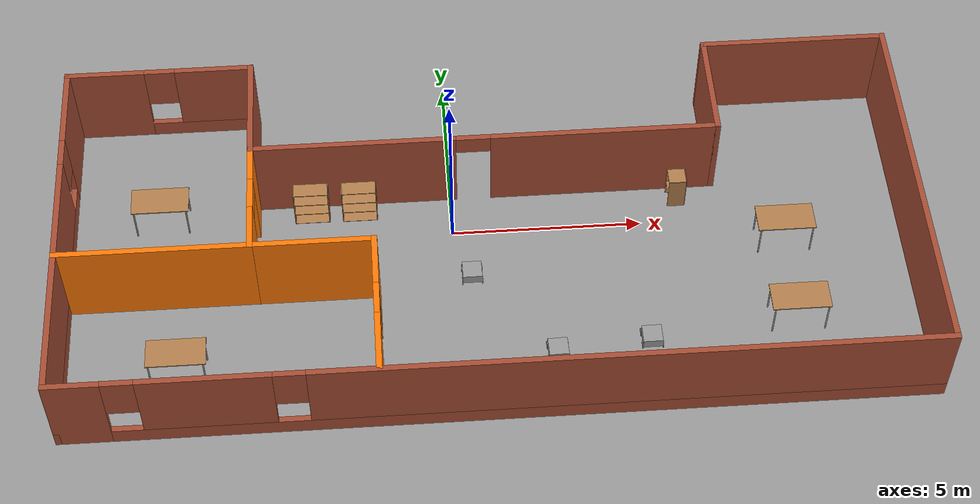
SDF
<sdf version="1.7">
 <world name="default">
  <plugin name="welcome_messgae" filename="libwelcome_message.so"/>
  <light name="sun" type="directional">
   <pose>0 0 10 0 -0 0</pose>
   <diffuse>0.8 0.8 0.8 1</diffuse>
   <specular>0.2 0.2 0.2 1</specular>
   <attenuation>
    <range>1000</range>
    <constant>0.9</constant>
    <linear>0.01</linear>
    <quadratic>0.001</quadratic>
   </attenuation>
   <direction>-0.5 0.1 -0.9</direction>
   <spot><inner_angle>0</inner_angle><outer_angle>0</outer_angle><falloff>0</falloff></spot>
  </light>
  <model name="ground_plane">
   <static>1</static>
   <link name="link">
    <collision name="collision">
     <geometry><plane><normal>0 0 1</normal><size>100 100</size></plane></geometry>
     <surface>
      <contact><collide_bitmask>65535</collide_bitmask></contact>
      <friction><ode><mu>100</mu><mu2>50</mu2></ode></friction>
     </surface>
    </collision>
    <visual name="visual">
     <cast_shadows>0</cast_shadows>
     <geometry><plane><normal>0 0 1</normal><size>100 100</size></plane></geometry>
     <material>
      <script><uri>file://media/materials/scripts/gazebo.material</uri><name>Gazebo/Grey</name></script>
     </material>
    </visual>
   </link>
  </model>
  <gravity>0 0 -9.8</gravity>
  <magnetic_field>6e-06 2.3e-05 -4.2e-05</magnetic_field>
  <atmosphere type="adiabatic"/>
  <physics type="ode">
   <max_step_size>0.001</max_step_size>
   <real_time_factor>1</real_time_factor>
   <real_time_update_rate>1000</real_time_update_rate>
  </physics>
  <scene><ambient>0.4 0.4 0.4 1</ambient><background>0.7 0.7 0.7 1</background><shadows>1</shadows></scene>
  <spherical_coordinates>
   <surface_model>EARTH_WGS84</surface_model>
   <latitude_deg>0</latitude_deg>
   <longitude_deg>0</longitude_deg>
   <elevation>0</elevation>
   <heading_deg>0</heading_deg>
  </spherical_coordinates>
  <model name="building1">
   <pose>0.94843 -0.891606 0 0 -0 0</pose>
   <link name="Wall_1">
    <pose>-10.925 0 0 0 -0 -1.5708</pose>
    <visual name="Wall_1_Visual_0">
     <pose>-3.84405 0 1.25 0 -0 0</pose>
     <geometry><box><size>2.31189 0.15 2.5</size></box></geometry>
     <material>
      <script><uri>file://media/materials/scripts/gazebo.material</uri><name>Gazebo/Bricks</name></script>
      <ambient>1 1 1 1</ambient>
     </material>
     <meta><layer>0</layer></meta>
    </visual>
    <collision name="Wall_1_Collision_0">
     <geometry><box><size>2.31189 0.15 2.5</size></box></geometry>
     <pose>-3.84405 0 1.25 0 -0 0</pose>
    </collision>
    <visual name="Wall_1_Visual_1">
     <pose>1.15595 0 0.25 0 -0 0</pose>
     <geometry><box><size>7.68811 0.15 0.5</size></box></geometry>
     <material>
      <script><uri>file://media/materials/scripts/gazebo.material</uri><name>Gazebo/Bricks</name></script>
      <ambient>1 1 1 1</ambient>
     </material>
     <meta><layer>0</layer></meta>
    </visual>
    <collision name="Wall_1_Collision_1">
     <geometry><box><size>7.68811 0.15 0.5</size></box></geometry>
     <pose>1.15595 0 0.25 0 -0 0</pose>
    </collision>
    <visual name="Wall_1_Visual_2">
     <pose>1.55594 0 1.5 0 -0 0</pose>
     <geometry><box><size>6.88811 0.15 2</size></box></geometry>
     <material>
      <script><uri>file://media/materials/scripts/gazebo.material</uri><name>Gazebo/Bricks</name></script>
      <ambient>1 1 1 1</ambient>
     </material>
     <meta><layer>0</layer></meta>
    </visual>
    <collision name="Wall_1_Collision_2">
     <geometry><box><size>6.88811 0.15 2</size></box></geometry>
     <pose>1.55594 0 1.5 0 -0 0</pose>
    </collision>
    <visual name="Wall_1_Visual_3">
     <pose>-2.28811 0 1.9 0 -0 0</pose>
     <geometry><box><size>0.8 0.15 1.2</size></box></geometry>
     <material>
      <script><uri>file://media/materials/scripts/gazebo.material</uri><name>Gazebo/Bricks</name></script>
      <ambient>1 1 1 1</ambient>
     </material>
     <meta><layer>0</layer></meta>
    </visual>
    <collision name="Wall_1_Collision_3">
     <geometry><box><size>0.8 0.15 1.2</size></box></geometry>
     <pose>-2.28811 0 1.9 0 -0 0</pose>
    </collision>
   </link>
   <link name="Wall_11">
    <pose>-6.075 0.525 0 0 -0 -1.5708</pose>
    <visual name="Wall_11_Visual_0">
     <pose>-1.08635 0 1.25 0 -0 0</pose>
     <geometry><box><size>1.07729 0.15 2.5</size></box></geometry>
     <material>
      <script><uri>file://media/materials/scripts/gazebo.material</uri><name>Gazebo/Grey</name></script>
      <ambient>0.996078 0.47451 0.0196078 1</ambient>
     </material>
     <meta><layer>0</layer></meta>
    </visual>
    <collision name="Wall_11_Collision_0">
     <geometry><box><size>1.07729 0.15 2.5</size></box></geometry>
     <pose>-1.08635 0 1.25 0 -0 0</pose>
    </collision>
    <visual name="Wall_11_Visual_1">
     <pose>0.988647 0 1.25 0 -0 0</pose>
     <geometry><box><size>1.27271 0.15 2.5</size></box></geometry>
     <material>
      <script><uri>file://media/materials/scripts/gazebo.material</uri><name>Gazebo/Grey</name></script>
      <ambient>0.996078 0.47451 0.0196078 1</ambient>
     </material>
     <meta><layer>0</layer></meta>
    </visual>
    <collision name="Wall_11_Collision_1">
     <geometry><box><size>1.27271 0.15 2.5</size></box></geometry>
     <pose>0.988647 0 1.25 0 -0 0</pose>
    </collision>
    <visual name="Wall_11_Visual_2">
     <pose>-0.097707 0 2.25 0 -0 0</pose>
     <geometry><box><size>0.9 0.15 0.5</size></box></geometry>
     <material>
      <script><uri>file://media/materials/scripts/gazebo.material</uri><name>Gazebo/Grey</name></script>
      <ambient>0.996078 0.47451 0.0196078 1</ambient>
     </material>
     <meta><layer>0</layer></meta>
    </visual>
    <collision name="Wall_11_Collision_2">
     <geometry><box><size>0.9 0.15 0.5</size></box></geometry>
     <pose>-0.097707 0 2.25 0 -0 0</pose>
    </collision>
   </link>
   <link name="Wall_12">
    <collision name="Wall_12_Collision">
     <geometry><box><size>3.25 0.15 2.5</size></box></geometry>
     <pose>0 0 1.25 0 -0 0</pose>
    </collision>
    <visual name="Wall_12_Visual">
     <pose>0 0 1.25 0 -0 0</pose>
     <geometry><box><size>3.25 0.15 2.5</size></box></geometry>
     <material>
      <script><uri>file://media/materials/scripts/gazebo.material</uri><name>Gazebo/Grey</name></script>
      <ambient>0.996078 0.47451 0.0196078 1</ambient>
     </material>
     <meta><layer>0</layer></meta>
    </visual>
    <pose>-4.525 -1.025 0 0 -0 0</pose>
   </link>
   <link name="Wall_13">
    <pose>-2.975 -2.95 0 0 -0 -1.5708</pose>
    <visual name="Wall_13_Visual_0">
     <pose>-1.27656 0 1.25 0 -0 0</pose>
     <geometry><box><size>1.44688 0.15 2.5</size></box></geometry>
     <material>
      <script><uri>file://media/materials/scripts/gazebo.material</uri><name>Gazebo/Grey</name></script>
      <ambient>0.996078 0.47451 0.0196078 1</ambient>
     </material>
     <meta><layer>0</layer></meta>
    </visual>
    <collision name="Wall_13_Collision_0">
     <geometry><box><size>1.44688 0.15 2.5</size></box></geometry>
     <pose>-1.27656 0 1.25 0 -0 0</pose>
    </collision>
    <visual name="Wall_13_Visual_1">
     <pose>1.17344 0 1.25 0 -0 0</pose>
     <geometry><box><size>1.65312 0.15 2.5</size></box></geometry>
     <material>
      <script><uri>file://media/materials/scripts/gazebo.material</uri><name>Gazebo/Grey</name></script>
      <ambient>0.996078 0.47451 0.0196078 1</ambient>
     </material>
     <meta><layer>0</layer></meta>
    </visual>
    <collision name="Wall_13_Collision_1">
     <geometry><box><size>1.65312 0.15 2.5</size></box></geometry>
     <pose>1.17344 0 1.25 0 -0 0</pose>
    </collision>
    <visual name="Wall_13_Visual_2">
     <pose>-0.103116 0 2.25 0 -0 0</pose>
     <geometry><box><size>0.9 0.15 0.5</size></box></geometry>
     <material>
      <script><uri>file://media/materials/scripts/gazebo.material</uri><name>Gazebo/Grey</name></script>
      <ambient>0.996078 0.47451 0.0196078 1</ambient>
     </material>
     <meta><layer>0</layer></meta>
    </visual>
    <collision name="Wall_13_Collision_2">
     <geometry><box><size>0.9 0.15 0.5</size></box></geometry>
     <pose>-0.103116 0 2.25 0 -0 0</pose>
    </collision>
   </link>
   <link name="Wall_15">
    <collision name="Wall_15_Collision">
     <geometry><box><size>5 0.15 2.5</size></box></geometry>
     <pose>0 0 1.25 0 -0 0</pose>
    </collision>
    <visual name="Wall_15_Visual">
     <pose>0 0 1.25 0 -0 0</pose>
     <geometry><box><size>5 0.15 2.5</size></box></geometry>
     <material>
      <script><uri>file://media/materials/scripts/gazebo.material</uri><name>Gazebo/Grey</name></script>
      <ambient>0.996078 0.47451 0.0196078 1</ambient>
     </material>
     <meta><layer>0</layer></meta>
    </visual>
    <pose>-8.5 -1.025 0 0 -0 3.14159</pose>
   </link>
   <link name="Wall_2">
    <pose>-0 -4.925 0 0 -0 0</pose>
    <visual name="Wall_2_Visual_0">
     <pose>-10.2951 0 1.25 0 -0 0</pose>
     <geometry><box><size>1.4098 0.15 2.5</size></box></geometry>
     <material>
      <script><uri>file://media/materials/scripts/gazebo.material</uri><name>Gazebo/Bricks</name></script>
      <ambient>1 1 1 1</ambient>
     </material>
     <meta><layer>0</layer></meta>
    </visual>
    <collision name="Wall_2_Collision_0">
     <geometry><box><size>1.4098 0.15 2.5</size></box></geometry>
     <pose>-10.2951 0 1.25 0 -0 0</pose>
    </collision>
    <visual name="Wall_2_Visual_1">
     <pose>0.704898 0 0.25 0 -0 0</pose>
     <geometry><box><size>20.5902 0.15 0.5</size></box></geometry>
     <material>
      <script><uri>file://media/materials/scripts/gazebo.material</uri><name>Gazebo/Bricks</name></script>
      <ambient>1 1 1 1</ambient>
     </material>
     <meta><layer>0</layer></meta>
    </visual>
    <collision name="Wall_2_Collision_1">
     <geometry><box><size>20.5902 0.15 0.5</size></box></geometry>
     <pose>0.704898 0 0.25 0 -0 0</pose>
    </collision>
    <visual name="Wall_2_Visual_2">
     <pose>-7.15471 0 1.5 0 -0 0</pose>
     <geometry><box><size>3.27099 0.15 2</size></box></geometry>
     <material>
      <script><uri>file://media/materials/scripts/gazebo.material</uri><name>Gazebo/Bricks</name></script>
      <ambient>1 1 1 1</ambient>
     </material>
     <meta><layer>0</layer></meta>
    </visual>
    <collision name="Wall_2_Collision_2">
     <geometry><box><size>3.27099 0.15 2</size></box></geometry>
     <pose>-7.15471 0 1.5 0 -0 0</pose>
    </collision>
    <visual name="Wall_2_Visual_3">
     <pose>3.14039 0 1.5 0 -0 0</pose>
     <geometry><box><size>15.7192 0.15 2</size></box></geometry>
     <material>
      <script><uri>file://media/materials/scripts/gazebo.material</uri><name>Gazebo/Bricks</name></script>
      <ambient>1 1 1 1</ambient>
     </material>
     <meta><layer>0</layer></meta>
    </visual>
    <collision name="Wall_2_Collision_3">
     <geometry><box><size>15.7192 0.15 2</size></box></geometry>
     <pose>3.14039 0 1.5 0 -0 0</pose>
    </collision>
    <visual name="Wall_2_Visual_4">
     <pose>-9.1902 0 1.9 0 -0 0</pose>
     <geometry><box><size>0.8 0.15 1.2</size></box></geometry>
     <material>
      <script><uri>file://media/materials/scripts/gazebo.material</uri><name>Gazebo/Bricks</name></script>
      <ambient>1 1 1 1</ambient>
     </material>
     <meta><layer>0</layer></meta>
    </visual>
    <collision name="Wall_2_Collision_4">
     <geometry><box><size>0.8 0.15 1.2</size></box></geometry>
     <pose>-9.1902 0 1.9 0 -0 0</pose>
    </collision>
    <visual name="Wall_2_Visual_5">
     <pose>-5.11922 0 1.9 0 -0 0</pose>
     <geometry><box><size>0.8 0.15 1.2</size></box></geometry>
     <material>
      <script><uri>file://media/materials/scripts/gazebo.material</uri><name>Gazebo/Bricks</name></script>
      <ambient>1 1 1 1</ambient>
     </material>
     <meta><layer>0</layer></meta>
    </visual>
    <collision name="Wall_2_Collision_5">
     <geometry><box><size>0.8 0.15 1.2</size></box></geometry>
     <pose>-5.11922 0 1.9 0 -0 0</pose>
    </collision>
   </link>
   <link name="Wall_3">
    <collision name="Wall_3_Collision">
     <geometry><box><size>10 0.15 2.5</size></box></geometry>
     <pose>0 0 1.25 0 -0 0</pose>
    </collision>
    <visual name="Wall_3_Visual">
     <pose>0 0 1.25 0 -0 0</pose>
     <geometry><box><size>10 0.15 2.5</size></box></geometry>
     <material>
      <script><uri>file://media/materials/scripts/gazebo.material</uri><name>Gazebo/Bricks</name></script>
      <ambient>1 1 1 1</ambient>
     </material>
     <meta><layer>0</layer></meta>
    </visual>
    <pose>10.925 0 0 0 -0 1.5708</pose>
   </link>
   <link name="Wall_4">
    <collision name="Wall_4_Collision">
     <geometry><box><size>5 0.15 2.5</size></box></geometry>
     <pose>0 0 1.25 0 -0 0</pose>
    </collision>
    <visual name="Wall_4_Visual">
     <pose>0 0 1.25 0 -0 0</pose>
     <geometry><box><size>5 0.15 2.5</size></box></geometry>
     <material>
      <script><uri>file://media/materials/scripts/gazebo.material</uri><name>Gazebo/Bricks</name></script>
      <ambient>1 1 1 1</ambient>
     </material>
     <meta><layer>0</layer></meta>
    </visual>
    <pose>8.5 4.925 0 0 -0 3.14159</pose>
   </link>
   <link name="Wall_5">
    <collision name="Wall_5_Collision">
     <geometry><box><size>3 0.15 2.5</size></box></geometry>
     <pose>0 0 1.25 0 -0 0</pose>
    </collision>
    <visual name="Wall_5_Visual">
     <pose>0 0 1.25 0 -0 0</pose>
     <geometry><box><size>3 0.15 2.5</size></box></geometry>
     <material>
      <script><uri>file://media/materials/scripts/gazebo.material</uri><name>Gazebo/Bricks</name></script>
      <ambient>1 1 1 1</ambient>
     </material>
     <meta><layer>0</layer></meta>
    </visual>
    <pose>6.075 3.5 0 0 -0 -1.5708</pose>
   </link>
   <link name="Wall_7">
    <pose>-8.5 4.925 0 0 -0 0</pose>
    <visual name="Wall_7_Visual_0">
     <pose>-1.44814 0 1.25 0 -0 0</pose>
     <geometry><box><size>2.10371 0.15 2.5</size></box></geometry>
     <material>
      <script><uri>file://media/materials/scripts/gazebo.material</uri><name>Gazebo/Bricks</name></script>
      <ambient>1 1 1 1</ambient>
     </material>
     <meta><layer>0</layer></meta>
    </visual>
    <collision name="Wall_7_Collision_0">
     <geometry><box><size>2.10371 0.15 2.5</size></box></geometry>
     <pose>-1.44814 0 1.25 0 -0 0</pose>
    </collision>
    <visual name="Wall_7_Visual_1">
     <pose>1.05186 0 0.25 0 -0 0</pose>
     <geometry><box><size>2.89629 0.15 0.5</size></box></geometry>
     <material>
      <script><uri>file://media/materials/scripts/gazebo.material</uri><name>Gazebo/Bricks</name></script>
      <ambient>1 1 1 1</ambient>
     </material>
     <meta><layer>0</layer></meta>
    </visual>
    <collision name="Wall_7_Collision_1">
     <geometry><box><size>2.89629 0.15 0.5</size></box></geometry>
     <pose>1.05186 0 0.25 0 -0 0</pose>
    </collision>
    <visual name="Wall_7_Visual_2">
     <pose>1.45186 0 1.5 0 -0 0</pose>
     <geometry><box><size>2.09629 0.15 2</size></box></geometry>
     <material>
      <script><uri>file://media/materials/scripts/gazebo.material</uri><name>Gazebo/Bricks</name></script>
      <ambient>1 1 1 1</ambient>
     </material>
     <meta><layer>0</layer></meta>
    </visual>
    <collision name="Wall_7_Collision_2">
     <geometry><box><size>2.09629 0.15 2</size></box></geometry>
     <pose>1.45186 0 1.5 0 -0 0</pose>
    </collision>
    <visual name="Wall_7_Visual_3">
     <pose>0.003714 0 1.9 0 -0 0</pose>
     <geometry><box><size>0.8 0.15 1.2</size></box></geometry>
     <material>
      <script><uri>file://media/materials/scripts/gazebo.material</uri><name>Gazebo/Bricks</name></script>
      <ambient>1 1 1 1</ambient>
     </material>
     <meta><layer>0</layer></meta>
    </visual>
    <collision name="Wall_7_Collision_3">
     <geometry><box><size>0.8 0.15 1.2</size></box></geometry>
     <pose>0.003714 0 1.9 0 -0 0</pose>
    </collision>
   </link>
   <link name="Wall_8">
    <collision name="Wall_8_Collision">
     <geometry><box><size>3 0.15 2.5</size></box></geometry>
     <pose>0 0 1.25 0 -0 0</pose>
    </collision>
    <visual name="Wall_8_Visual">
     <pose>0 0 1.25 0 -0 0</pose>
     <geometry><box><size>3 0.15 2.5</size></box></geometry>
     <material>
      <script><uri>file://media/materials/scripts/gazebo.material</uri><name>Gazebo/Bricks</name></script>
      <ambient>1 1 1 1</ambient>
     </material>
     <meta><layer>0</layer></meta>
    </visual>
    <pose>-6.075 3.5 0 0 -0 -1.5708</pose>
   </link>
   <link name="Wall_9">
    <pose>-0.025 2.075 0 0 -0 0</pose>
    <visual name="Wall_9_Visual_0">
     <pose>-3.42903 0 1.25 0 -0 0</pose>
     <geometry><box><size>5.39195 0.15 2.5</size></box></geometry>
     <material>
      <script><uri>file://media/materials/scripts/gazebo.material</uri><name>Gazebo/Bricks</name></script>
      <ambient>1 1 1 1</ambient>
     </material>
     <meta><layer>0</layer></meta>
    </visual>
    <collision name="Wall_9_Collision_0">
     <geometry><box><size>5.39195 0.15 2.5</size></box></geometry>
     <pose>-3.42903 0 1.25 0 -0 0</pose>
    </collision>
    <visual name="Wall_9_Visual_1">
     <pose>3.14597 0 1.25 0 -0 0</pose>
     <geometry><box><size>5.95805 0.15 2.5</size></box></geometry>
     <material>
      <script><uri>file://media/materials/scripts/gazebo.material</uri><name>Gazebo/Bricks</name></script>
      <ambient>1 1 1 1</ambient>
     </material>
     <meta><layer>0</layer></meta>
    </visual>
    <collision name="Wall_9_Collision_1">
     <geometry><box><size>5.95805 0.15 2.5</size></box></geometry>
     <pose>3.14597 0 1.25 0 -0 0</pose>
    </collision>
    <visual name="Wall_9_Visual_2">
     <pose>-0.283051 0 2.25 0 -0 0</pose>
     <geometry><box><size>0.9 0.15 0.5</size></box></geometry>
     <material>
      <script><uri>file://media/materials/scripts/gazebo.material</uri><name>Gazebo/Bricks</name></script>
      <ambient>1 1 1 1</ambient>
     </material>
     <meta><layer>0</layer></meta>
    </visual>
    <collision name="Wall_9_Collision_2">
     <geometry><box><size>0.9 0.15 0.5</size></box></geometry>
     <pose>-0.283051 0 2.25 0 -0 0</pose>
    </collision>
   </link>
   <static>1</static>
  </model>
  <model name="ground_plane_0">
   <static>1</static>
   <link name="link">
    <collision name="collision">
     <geometry><plane><normal>0 0 1</normal><size>100 100</size></plane></geometry>
     <surface>
      <contact><collide_bitmask>65535</collide_bitmask></contact>
      <friction><ode><mu>100</mu><mu2>50</mu2></ode></friction>
     </surface>
    </collision>
    <visual name="visual">
     <cast_shadows>0</cast_shadows>
     <geometry><plane><normal>0 0 1</normal><size>100 100</size></plane></geometry>
     <material>
      <script><uri>file://media/materials/scripts/gazebo.material</uri><name>Gazebo/Grey</name></script>
     </material>
    </visual>
   </link>
   <pose>9.22841 12.0339 0 0 -0 0</pose>
  </model>
  <model name="bookshelf">
   <static>1</static>
   <link name="link">
    <inertial><mass>1</mass></inertial>
    <collision name="back">
     <pose>0 0.005 0.6 0 -0 0</pose>
     <geometry><box><size>0.9 0.01 1.2</size></box></geometry>
    </collision>
    <visual name="visual1">
     <pose>0 0.005 0.6 0 -0 0</pose>
     <geometry><box><size>0.9 0.01 1.2</size></box></geometry>
     <material>
      <script><uri>file://media/materials/scripts/gazebo.material</uri><name>Gazebo/Wood</name></script>
     </material>
    </visual>
    <collision name="left_side">
     <pose>0.45 -0.195 0.6 0 -0 0</pose>
     <geometry><box><size>0.02 0.4 1.2</size></box></geometry>
    </collision>
    <visual name="visual2">
     <pose>0.45 -0.195 0.6 0 -0 0</pose>
     <geometry><box><size>0.02 0.4 1.2</size></box></geometry>
     <material>
      <script><uri>file://media/materials/scripts/gazebo.material</uri><name>Gazebo/Wood</name></script>
     </material>
    </visual>
    <collision name="right_side">
     <pose>-0.45 -0.195 0.6 0 -0 0</pose>
     <geometry><box><size>0.02 0.4 1.2</size></box></geometry>
    </collision>
    <visual name="visual3">
     <pose>-0.45 -0.195 0.6 0 -0 0</pose>
     <geometry><box><size>0.02 0.4 1.2</size></box></geometry>
     <material>
      <script><uri>file://media/materials/scripts/gazebo.material</uri><name>Gazebo/Wood</name></script>
     </material>
    </visual>
    <collision name="bottom">
     <pose>0 -0.195 0.03 0 -0 0</pose>
     <geometry><box><size>0.88 0.4 0.06</size></box></geometry>
    </collision>
    <visual name="visual4">
     <pose>0 -0.195 0.03 0 -0 0</pose>
     <geometry><box><size>0.88 0.4 0.06</size></box></geometry>
     <material>
      <script><uri>file://media/materials/scripts/gazebo.material</uri><name>Gazebo/Wood</name></script>
     </material>
    </visual>
    <collision name="top">
     <pose>0 -0.195 1.19 0 -0 0</pose>
     <geometry><box><size>0.88 0.4 0.02</size></box></geometry>
    </collision>
    <visual name="visual5">
     <pose>0 -0.195 1.19 0 -0 0</pose>
     <geometry><box><size>0.88 0.4 0.02</size></box></geometry>
     <material>
      <script><uri>file://media/materials/scripts/gazebo.material</uri><name>Gazebo/Wood</name></script>
     </material>
    </visual>
    <collision name="low_shelf">
     <pose>0 -0.195 0.43 0 -0 0</pose>
     <geometry><box><size>0.88 0.4 0.02</size></box></geometry>
    </collision>
    <visual name="visual6">
     <pose>0 -0.195 0.43 0 -0 0</pose>
     <geometry><box><size>0.88 0.4 0.02</size></box></geometry>
     <material>
      <script><uri>file://media/materials/scripts/gazebo.material</uri><name>Gazebo/Wood</name></script>
     </material>
    </visual>
    <collision name="high_shelf">
     <pose>0 -0.195 0.8 0 -0 0</pose>
     <geometry><box><size>0.88 0.4 0.02</size></box></geometry>
    </collision>
    <visual name="visual7">
     <pose>0 -0.195 0.8 0 -0 0</pose>
     <geometry><box><size>0.88 0.4 0.02</size></box></geometry>
     <material>
      <script><uri>file://media/materials/scripts/gazebo.material</uri><name>Gazebo/Wood</name></script>
     </material>
    </visual>
   </link>
   <pose>-3.67466 0.963506 0 0 -0 0</pose>
  </model>
  <model name="bookshelf_0">
   <static>1</static>
   <link name="link">
    <inertial><mass>1</mass></inertial>
    <collision name="back">
     <pose>0 0.005 0.6 0 -0 0</pose>
     <geometry><box><size>0.9 0.01 1.2</size></box></geometry>
    </collision>
    <visual name="visual1">
     <pose>0 0.005 0.6 0 -0 0</pose>
     <geometry><box><size>0.9 0.01 1.2</size></box></geometry>
     <material>
      <script><uri>file://media/materials/scripts/gazebo.material</uri><name>Gazebo/Wood</name></script>
     </material>
    </visual>
    <collision name="left_side">
     <pose>0.45 -0.195 0.6 0 -0 0</pose>
     <geometry><box><size>0.02 0.4 1.2</size></box></geometry>
    </collision>
    <visual name="visual2">
     <pose>0.45 -0.195 0.6 0 -0 0</pose>
     <geometry><box><size>0.02 0.4 1.2</size></box></geometry>
     <material>
      <script><uri>file://media/materials/scripts/gazebo.material</uri><name>Gazebo/Wood</name></script>
     </material>
    </visual>
    <collision name="right_side">
     <pose>-0.45 -0.195 0.6 0 -0 0</pose>
     <geometry><box><size>0.02 0.4 1.2</size></box></geometry>
    </collision>
    <visual name="visual3">
     <pose>-0.45 -0.195 0.6 0 -0 0</pose>
     <geometry><box><size>0.02 0.4 1.2</size></box></geometry>
     <material>
      <script><uri>file://media/materials/scripts/gazebo.material</uri><name>Gazebo/Wood</name></script>
     </material>
    </visual>
    <collision name="bottom">
     <pose>0 -0.195 0.03 0 -0 0</pose>
     <geometry><box><size>0.88 0.4 0.06</size></box></geometry>
    </collision>
    <visual name="visual4">
     <pose>0 -0.195 0.03 0 -0 0</pose>
     <geometry><box><size>0.88 0.4 0.06</size></box></geometry>
     <material>
      <script><uri>file://media/materials/scripts/gazebo.material</uri><name>Gazebo/Wood</name></script>
     </material>
    </visual>
    <collision name="top">
     <pose>0 -0.195 1.19 0 -0 0</pose>
     <geometry><box><size>0.88 0.4 0.02</size></box></geometry>
    </collision>
    <visual name="visual5">
     <pose>0 -0.195 1.19 0 -0 0</pose>
     <geometry><box><size>0.88 0.4 0.02</size></box></geometry>
     <material>
      <script><uri>file://media/materials/scripts/gazebo.material</uri><name>Gazebo/Wood</name></script>
     </material>
    </visual>
    <collision name="low_shelf">
     <pose>0 -0.195 0.43 0 -0 0</pose>
     <geometry><box><size>0.88 0.4 0.02</size></box></geometry>
    </collision>
    <visual name="visual6">
     <pose>0 -0.195 0.43 0 -0 0</pose>
     <geometry><box><size>0.88 0.4 0.02</size></box></geometry>
     <material>
      <script><uri>file://media/materials/scripts/gazebo.material</uri><name>Gazebo/Wood</name></script>
     </material>
    </visual>
    <collision name="high_shelf">
     <pose>0 -0.195 0.8 0 -0 0</pose>
     <geometry><box><size>0.88 0.4 0.02</size></box></geometry>
    </collision>
    <visual name="visual7">
     <pose>0 -0.195 0.8 0 -0 0</pose>
     <geometry><box><size>0.88 0.4 0.02</size></box></geometry>
     <material>
      <script><uri>file://media/materials/scripts/gazebo.material</uri><name>Gazebo/Wood</name></script>
     </material>
    </visual>
   </link>
   <pose>-2.41323 0.949971 0 0 -0 0</pose>
  </model>
  <model name="cabinet">
   <static>1</static>
   <link name="cabinet_bottom_plate">
    <inertial>
     <pose>0 0 -1 0 -0 0</pose>
     <inertia><ixx>2.05</ixx><ixy>0</ixy><ixz>0</ixz><iyy>2.05</iyy><iyz>0</iyz><izz>2.05</izz></inertia>
     <mass>25</mass>
    </inertial>
    <collision name="cabinet_bottom_plate_geom">
     <pose>0 0 0.01 0 -0 0</pose>
     <geometry><box><size>0.45 0.45 0.02</size></box></geometry>
    </collision>
    <visual name="cabinet_bottom_plate_geom_visual">
     <pose>0 0 0.01 0 -0 0</pose>
     <geometry><box><size>0.45 0.45 0.02</size></box></geometry>
     <material>
      <script><uri>file://media/materials/scripts/gazebo.material</uri><name>Gazebo/Wood</name></script>
     </material>
    </visual>
    <collision name="cabinet_bottom_plate_geom_cabinet_back_plate">
     <pose>0.235 0 0.51 0 -0 0</pose>
     <geometry><box><size>0.02 0.45 1.02</size></box></geometry>
    </collision>
    <visual name="cabinet_bottom_plate_geom_cabinet_back_plate_visual">
     <pose>0.235 0 0.51 0 -0 0</pose>
     <geometry><box><size>0.02 0.45 1.02</size></box></geometry>
     <material>
      <script><uri>file://media/materials/scripts/gazebo.material</uri><name>Gazebo/Wood</name></script>
     </material>
    </visual>
    <collision name="cabinet_bottom_plate_geom_cabinet_left_plate">
     <pose>0 0.235 0.51 0 -0 0</pose>
     <geometry><box><size>0.45 0.02 1.02</size></box></geometry>
    </collision>
    <visual name="cabinet_bottom_plate_geom_cabinet_left_plate_visual">
     <pose>0 0.235 0.51 0 -0 0</pose>
     <geometry><box><size>0.45 0.02 1.02</size></box></geometry>
     <material>
      <script><uri>file://media/materials/scripts/gazebo.material</uri><name>Gazebo/Wood</name></script>
     </material>
    </visual>
    <collision name="cabinet_bottom_plate_geom_cabinet_middle_plate">
     <pose>0 0 0.51 0 -0 0</pose>
     <geometry><box><size>0.45 0.45 0.02</size></box></geometry>
    </collision>
    <visual name="cabinet_bottom_plate_geom_cabinet_middle_plate_visual">
     <pose>0 0 0.51 0 -0 0</pose>
     <geometry><box><size>0.45 0.45 0.02</size></box></geometry>
     <material>
      <script><uri>file://media/materials/scripts/gazebo.material</uri><name>Gazebo/Wood</name></script>
     </material>
    </visual>
    <collision name="cabinet_bottom_plate_geom_cabinet_right_plate">
     <pose>0 -0.235 0.51 0 -0 0</pose>
     <geometry><box><size>0.45 0.02 1.02</size></box></geometry>
    </collision>
    <visual name="cabinet_bottom_plate_geom_cabinet_right_plate_visual">
     <pose>0 -0.235 0.51 0 -0 0</pose>
     <geometry><box><size>0.45 0.02 1.02</size></box></geometry>
     <material>
      <script><uri>file://media/materials/scripts/gazebo.material</uri><name>Gazebo/Wood</name></script>
     </material>
    </visual>
    <collision name="cabinet_bottom_plate_geom_cabinet_top_plate">
     <pose>0 0 1.01 0 -0 0</pose>
     <geometry><box><size>0.45 0.45 0.02</size></box></geometry>
    </collision>
    <visual name="cabinet_bottom_plate_geom_cabinet_top_plate_visual">
     <pose>0 0 1.01 0 -0 0</pose>
     <geometry><box><size>0.45 0.45 0.02</size></box></geometry>
     <material>
      <script><uri>file://media/materials/scripts/gazebo.material</uri><name>Gazebo/Wood</name></script>
     </material>
    </visual>
   </link>
   <pose>6.0025 0.743217 0 0 -0 0</pose>
  </model>
  <model name="table">
   <static>1</static>
   <link name="link">
    <collision name="surface">
     <pose>0 0 1 0 -0 0</pose>
     <geometry><box><size>1.5 0.8 0.03</size></box></geometry>
     <surface><friction><ode><mu>0.6</mu><mu2>0.6</mu2></ode></friction></surface>
    </collision>
    <visual name="visual1">
     <pose>0 0 1 0 -0 0</pose>
     <geometry><box><size>1.5 0.8 0.03</size></box></geometry>
     <material>
      <script><uri>file://media/materials/scripts/gazebo.material</uri><name>Gazebo/Wood</name></script>
     </material>
    </visual>
    <collision name="front_left_leg">
     <pose>0.68 0.38 0.5 0 -0 0</pose>
     <geometry><cylinder><radius>0.02</radius><length>1</length></cylinder></geometry>
    </collision>
    <visual name="front_left_leg">
     <pose>0.68 0.38 0.5 0 -0 0</pose>
     <geometry><cylinder><radius>0.02</radius><length>1</length></cylinder></geometry>
     <material>
      <script><uri>file://media/materials/scripts/gazebo.material</uri><name>Gazebo/Grey</name></script>
     </material>
    </visual>
    <collision name="front_right_leg">
     <pose>0.68 -0.38 0.5 0 -0 0</pose>
     <geometry><cylinder><radius>0.02</radius><length>1</length></cylinder></geometry>
    </collision>
    <visual name="front_right_leg">
     <pose>0.68 -0.38 0.5 0 -0 0</pose>
     <geometry><cylinder><radius>0.02</radius><length>1</length></cylinder></geometry>
     <material>
      <script><uri>file://media/materials/scripts/gazebo.material</uri><name>Gazebo/Grey</name></script>
     </material>
    </visual>
    <collision name="back_right_leg">
     <pose>-0.68 -0.38 0.5 0 -0 0</pose>
     <geometry><cylinder><radius>0.02</radius><length>1</length></cylinder></geometry>
    </collision>
    <visual name="back_right_leg">
     <pose>-0.68 -0.38 0.5 0 -0 0</pose>
     <geometry><cylinder><radius>0.02</radius><length>1</length></cylinder></geometry>
     <material>
      <script><uri>file://media/materials/scripts/gazebo.material</uri><name>Gazebo/Grey</name></script>
     </material>
    </visual>
    <collision name="back_left_leg">
     <pose>-0.68 0.38 0.5 0 -0 0</pose>
     <geometry><cylinder><radius>0.02</radius><length>1</length></cylinder></geometry>
    </collision>
    <visual name="back_left_leg">
     <pose>-0.68 0.38 0.5 0 -0 0</pose>
     <geometry><cylinder><radius>0.02</radius><length>1</length></cylinder></geometry>
     <material>
      <script><uri>file://media/materials/scripts/gazebo.material</uri><name>Gazebo/Grey</name></script>
     </material>
    </visual>
   </link>
   <pose>8.6565 -0.81394 0 0 -0 0</pose>
  </model>
  <model name="table_0">
   <static>1</static>
   <link name="link">
    <collision name="surface">
     <pose>0 0 1 0 -0 0</pose>
     <geometry><box><size>1.5 0.8 0.03</size></box></geometry>
     <surface><friction><ode><mu>0.6</mu><mu2>0.6</mu2></ode></friction></surface>
    </collision>
    <visual name="visual1">
     <pose>0 0 1 0 -0 0</pose>
     <geometry><box><size>1.5 0.8 0.03</size></box></geometry>
     <material>
      <script><uri>file://media/materials/scripts/gazebo.material</uri><name>Gazebo/Wood</name></script>
     </material>
    </visual>
    <collision name="front_left_leg">
     <pose>0.68 0.38 0.5 0 -0 0</pose>
     <geometry><cylinder><radius>0.02</radius><length>1</length></cylinder></geometry>
    </collision>
    <visual name="front_left_leg">
     <pose>0.68 0.38 0.5 0 -0 0</pose>
     <geometry><cylinder><radius>0.02</radius><length>1</length></cylinder></geometry>
     <material>
      <script><uri>file://media/materials/scripts/gazebo.material</uri><name>Gazebo/Grey</name></script>
     </material>
    </visual>
    <collision name="front_right_leg">
     <pose>0.68 -0.38 0.5 0 -0 0</pose>
     <geometry><cylinder><radius>0.02</radius><length>1</length></cylinder></geometry>
    </collision>
    <visual name="front_right_leg">
     <pose>0.68 -0.38 0.5 0 -0 0</pose>
     <geometry><cylinder><radius>0.02</radius><length>1</length></cylinder></geometry>
     <material>
      <script><uri>file://media/materials/scripts/gazebo.material</uri><name>Gazebo/Grey</name></script>
     </material>
    </visual>
    <collision name="back_right_leg">
     <pose>-0.68 -0.38 0.5 0 -0 0</pose>
     <geometry><cylinder><radius>0.02</radius><length>1</length></cylinder></geometry>
    </collision>
    <visual name="back_right_leg">
     <pose>-0.68 -0.38 0.5 0 -0 0</pose>
     <geometry><cylinder><radius>0.02</radius><length>1</length></cylinder></geometry>
     <material>
      <script><uri>file://media/materials/scripts/gazebo.material</uri><name>Gazebo/Grey</name></script>
     </material>
    </visual>
    <collision name="back_left_leg">
     <pose>-0.68 0.38 0.5 0 -0 0</pose>
     <geometry><cylinder><radius>0.02</radius><length>1</length></cylinder></geometry>
    </collision>
    <visual name="back_left_leg">
     <pose>-0.68 0.38 0.5 0 -0 0</pose>
     <geometry><cylinder><radius>0.02</radius><length>1</length></cylinder></geometry>
     <material>
      <script><uri>file://media/materials/scripts/gazebo.material</uri><name>Gazebo/Grey</name></script>
     </material>
    </visual>
   </link>
   <pose>8.64335 -3.33372 0 0 -0 0</pose>
  </model>
  <model name="table_1">
   <static>1</static>
   <link name="link">
    <collision name="surface">
     <pose>0 0 1 0 -0 0</pose>
     <geometry><box><size>1.5 0.8 0.03</size></box></geometry>
     <surface><friction><ode><mu>0.6</mu><mu2>0.6</mu2></ode></friction></surface>
    </collision>
    <visual name="visual1">
     <pose>0 0 1 0 -0 0</pose>
     <geometry><box><size>1.5 0.8 0.03</size></box></geometry>
     <material>
      <script><uri>file://media/materials/scripts/gazebo.material</uri><name>Gazebo/Wood</name></script>
     </material>
    </visual>
    <collision name="front_left_leg">
     <pose>0.68 0.38 0.5 0 -0 0</pose>
     <geometry><cylinder><radius>0.02</radius><length>1</length></cylinder></geometry>
    </collision>
    <visual name="front_left_leg">
     <pose>0.68 0.38 0.5 0 -0 0</pose>
     <geometry><cylinder><radius>0.02</radius><length>1</length></cylinder></geometry>
     <material>
      <script><uri>file://media/materials/scripts/gazebo.material</uri><name>Gazebo/Grey</name></script>
     </material>
    </visual>
    <collision name="front_right_leg">
     <pose>0.68 -0.38 0.5 0 -0 0</pose>
     <geometry><cylinder><radius>0.02</radius><length>1</length></cylinder></geometry>
    </collision>
    <visual name="front_right_leg">
     <pose>0.68 -0.38 0.5 0 -0 0</pose>
     <geometry><cylinder><radius>0.02</radius><length>1</length></cylinder></geometry>
     <material>
      <script><uri>file://media/materials/scripts/gazebo.material</uri><name>Gazebo/Grey</name></script>
     </material>
    </visual>
    <collision name="back_right_leg">
     <pose>-0.68 -0.38 0.5 0 -0 0</pose>
     <geometry><cylinder><radius>0.02</radius><length>1</length></cylinder></geometry>
    </collision>
    <visual name="back_right_leg">
     <pose>-0.68 -0.38 0.5 0 -0 0</pose>
     <geometry><cylinder><radius>0.02</radius><length>1</length></cylinder></geometry>
     <material>
      <script><uri>file://media/materials/scripts/gazebo.material</uri><name>Gazebo/Grey</name></script>
     </material>
    </visual>
    <collision name="back_left_leg">
     <pose>-0.68 0.38 0.5 0 -0 0</pose>
     <geometry><cylinder><radius>0.02</radius><length>1</length></cylinder></geometry>
    </collision>
    <visual name="back_left_leg">
     <pose>-0.68 0.38 0.5 0 -0 0</pose>
     <geometry><cylinder><radius>0.02</radius><length>1</length></cylinder></geometry>
     <material>
      <script><uri>file://media/materials/scripts/gazebo.material</uri><name>Gazebo/Grey</name></script>
     </material>
    </visual>
   </link>
   <pose>-7.07568 -4.00827 0 0 -0 0</pose>
  </model>
  <model name="table_2">
   <static>1</static>
   <link name="link">
    <collision name="surface">
     <pose>0 0 1 0 -0 0</pose>
     <geometry><box><size>1.5 0.8 0.03</size></box></geometry>
     <surface><friction><ode><mu>0.6</mu><mu2>0.6</mu2></ode></friction></surface>
    </collision>
    <visual name="visual1">
     <pose>0 0 1 0 -0 0</pose>
     <geometry><box><size>1.5 0.8 0.03</size></box></geometry>
     <material>
      <script><uri>file://media/materials/scripts/gazebo.material</uri><name>Gazebo/Wood</name></script>
     </material>
    </visual>
    <collision name="front_left_leg">
     <pose>0.68 0.38 0.5 0 -0 0</pose>
     <geometry><cylinder><radius>0.02</radius><length>1</length></cylinder></geometry>
    </collision>
    <visual name="front_left_leg">
     <pose>0.68 0.38 0.5 0 -0 0</pose>
     <geometry><cylinder><radius>0.02</radius><length>1</length></cylinder></geometry>
     <material>
      <script><uri>file://media/materials/scripts/gazebo.material</uri><name>Gazebo/Grey</name></script>
     </material>
    </visual>
    <collision name="front_right_leg">
     <pose>0.68 -0.38 0.5 0 -0 0</pose>
     <geometry><cylinder><radius>0.02</radius><length>1</length></cylinder></geometry>
    </collision>
    <visual name="front_right_leg">
     <pose>0.68 -0.38 0.5 0 -0 0</pose>
     <geometry><cylinder><radius>0.02</radius><length>1</length></cylinder></geometry>
     <material>
      <script><uri>file://media/materials/scripts/gazebo.material</uri><name>Gazebo/Grey</name></script>
     </material>
    </visual>
    <collision name="back_right_leg">
     <pose>-0.68 -0.38 0.5 0 -0 0</pose>
     <geometry><cylinder><radius>0.02</radius><length>1</length></cylinder></geometry>
    </collision>
    <visual name="back_right_leg">
     <pose>-0.68 -0.38 0.5 0 -0 0</pose>
     <geometry><cylinder><radius>0.02</radius><length>1</length></cylinder></geometry>
     <material>
      <script><uri>file://media/materials/scripts/gazebo.material</uri><name>Gazebo/Grey</name></script>
     </material>
    </visual>
    <collision name="back_left_leg">
     <pose>-0.68 0.38 0.5 0 -0 0</pose>
     <geometry><cylinder><radius>0.02</radius><length>1</length></cylinder></geometry>
    </collision>
    <visual name="back_left_leg">
     <pose>-0.68 0.38 0.5 0 -0 0</pose>
     <geometry><cylinder><radius>0.02</radius><length>1</length></cylinder></geometry>
     <material>
      <script><uri>file://media/materials/scripts/gazebo.material</uri><name>Gazebo/Grey</name></script>
     </material>
    </visual>
   </link>
   <pose>-7.61434 0.831494 0 0 -0 0</pose>
  </model>
  <model name="four_wheeled_robot">
   <link name="link_2">
    <inertial>
     <mass>1</mass>
     <inertia>
      <ixx>0.166667</ixx>
      <ixy>0</ixy>
      <ixz>0</ixz>
      <iyy>0.166667</iyy>
      <iyz>0</iyz>
      <izz>0.166667</izz>
     </inertia>
    </inertial>
    <pose>-9.6e-05 0 0.05 0 -0 0</pose>
    <visual name="visual">
     <geometry><box><size>0.5 0.5 0.25</size></box></geometry>
     <material>
      <lighting>1</lighting>
      <script><uri>file://media/materials/scripts/gazebo.material</uri><name>Gazebo/Grey</name></script>
      <shader type="pixel"><normal_map>__default__</normal_map></shader>
      <ambient>0.3 0.3 0.3 1</ambient>
      <diffuse>0.7 0.7 0.7 1</diffuse>
      <specular>0.01 0.01 0.01 1</specular>
      <emissive>0 0 0 1</emissive>
     </material>
    </visual>
    <collision name="collision">
     <geometry><box><size>0.5 0.5 0.25</size></box></geometry>
     <surface>
      <friction>
       <ode><mu>1</mu><mu2>1</mu2><fdir1>0 0 0</fdir1><slip1>0</slip1><slip2>0</slip2></ode>
       <torsional>
        <coefficient>1</coefficient>
        <patch_radius>0</patch_radius>
        <surface_radius>0</surface_radius>
        <use_patch_radius>1</use_patch_radius>
        <ode><slip>0</slip></ode>
       </torsional>
      </friction>
      <bounce><restitution_coefficient>0</restitution_coefficient><threshold>1e+06</threshold></bounce>
      <contact>
       <collide_without_contact>0</collide_without_contact>
       <collide_without_contact_bitmask>1</collide_without_contact_bitmask>
       <collide_bitmask>1</collide_bitmask>
       <ode>
        <soft_cfm>0</soft_cfm>
        <soft_erp>0.2</soft_erp>
        <kp>1e+13</kp>
        <kd>1</kd>
        <max_vel>0.01</max_vel>
        <min_depth>0</min_depth>
       </ode>
       <bullet>
        <split_impulse>1</split_impulse>
        <split_impulse_penetration_threshold>-0.01</split_impulse_penetration_threshold>
        <soft_cfm>0</soft_cfm>
        <soft_erp>0.2</soft_erp>
        <kp>1e+13</kp>
        <kd>1</kd>
       </bullet>
      </contact>
     </surface>
    </collision>
   </link>
   <link name="link_3">
    <inertial>
     <mass>1</mass>
     <inertia><ixx>0.145833</ixx><ixy>0</ixy><ixz>0</ixz><iyy>0.145833</iyy><iyz>0</iyz><izz>0.125</izz></inertia>
    </inertial>
    <pose>0.260404 -0.2 -0.05 1.5707 0 1.5707</pose>
    <visual name="visual">
     <geometry><cylinder><radius>0.1</radius><length>0.02</length></cylinder></geometry>
     <material>
      <lighting>1</lighting>
      <script><uri>file://media/materials/scripts/gazebo.material</uri><name>Gazebo/Grey</name></script>
      <shader type="pixel"><normal_map>__default__</normal_map></shader>
      <ambient>0.3 0.3 0.3 1</ambient>
      <diffuse>0.7 0.7 0.7 1</diffuse>
      <specular>0.01 0.01 0.01 1</specular>
      <emissive>0 0 0 1</emissive>
     </material>
    </visual>
    <collision name="collision">
     <geometry><cylinder><radius>0.1</radius><length>0.02</length></cylinder></geometry>
     <surface>
      <friction>
       <ode><mu>1</mu><mu2>1</mu2><fdir1>0 0 0</fdir1><slip1>0</slip1><slip2>0</slip2></ode>
       <torsional>
        <coefficient>1</coefficient>
        <patch_radius>0</patch_radius>
        <surface_radius>0</surface_radius>
        <use_patch_radius>1</use_patch_radius>
        <ode><slip>0</slip></ode>
       </torsional>
      </friction>
      <bounce><restitution_coefficient>0</restitution_coefficient><threshold>1e+06</threshold></bounce>
      <contact>
       <collide_without_contact>0</collide_without_contact>
       <collide_without_contact_bitmask>1</collide_without_contact_bitmask>
       <collide_bitmask>1</collide_bitmask>
       <ode>
        <soft_cfm>0</soft_cfm>
        <soft_erp>0.2</soft_erp>
        <kp>1e+13</kp>
        <kd>1</kd>
        <max_vel>0.01</max_vel>
        <min_depth>0</min_depth>
       </ode>
       <bullet>
        <split_impulse>1</split_impulse>
        <split_impulse_penetration_threshold>-0.01</split_impulse_penetration_threshold>
        <soft_cfm>0</soft_cfm>
        <soft_erp>0.2</soft_erp>
        <kp>1e+13</kp>
        <kd>1</kd>
       </bullet>
      </contact>
     </surface>
    </collision>
   </link>
   <link name="link_3_clone">
    <inertial>
     <mass>1</mass>
     <inertia><ixx>0.145833</ixx><ixy>0</ixy><ixz>0</ixz><iyy>0.145833</iyy><iyz>0</iyz><izz>0.125</izz></inertia>
    </inertial>
    <pose>-0.260115 0.2 -0.05 1.5707 0 1.5707</pose>
    <visual name="visual">
     <geometry><cylinder><radius>0.1</radius><length>0.02</length></cylinder></geometry>
     <material>
      <lighting>1</lighting>
      <script><uri>file://media/materials/scripts/gazebo.material</uri><name>Gazebo/Grey</name></script>
      <shader type="pixel"><normal_map>__default__</normal_map></shader>
      <ambient>0.3 0.3 0.3 1</ambient>
      <diffuse>0.7 0.7 0.7 1</diffuse>
      <specular>0.01 0.01 0.01 1</specular>
      <emissive>0 0 0 1</emissive>
     </material>
    </visual>
    <collision name="collision">
     <geometry><cylinder><radius>0.1</radius><length>0.02</length></cylinder></geometry>
     <surface>
      <friction>
       <ode><mu>1</mu><mu2>1</mu2><fdir1>0 0 0</fdir1><slip1>0</slip1><slip2>0</slip2></ode>
       <torsional>
        <coefficient>1</coefficient>
        <patch_radius>0</patch_radius>
        <surface_radius>0</surface_radius>
        <use_patch_radius>1</use_patch_radius>
        <ode><slip>0</slip></ode>
       </torsional>
      </friction>
      <bounce><restitution_coefficient>0</restitution_coefficient><threshold>1e+06</threshold></bounce>
      <contact>
       <collide_without_contact>0</collide_without_contact>
       <collide_without_contact_bitmask>1</collide_without_contact_bitmask>
       <collide_bitmask>1</collide_bitmask>
       <ode>
        <soft_cfm>0</soft_cfm>
        <soft_erp>0.2</soft_erp>
        <kp>1e+13</kp>
        <kd>1</kd>
        <max_vel>0.01</max_vel>
        <min_depth>0</min_depth>
       </ode>
       <bullet>
        <split_impulse>1</split_impulse>
        <split_impulse_penetration_threshold>-0.01</split_impulse_penetration_threshold>
        <soft_cfm>0</soft_cfm>
        <soft_erp>0.2</soft_erp>
        <kp>1e+13</kp>
        <kd>1</kd>
       </bullet>
      </contact>
     </surface>
    </collision>
   </link>
   <link name="link_3_clone_0">
    <inertial>
     <mass>1</mass>
     <inertia><ixx>0.145833</ixx><ixy>0</ixy><ixz>0</ixz><iyy>0.145833</iyy><iyz>0</iyz><izz>0.125</izz></inertia>
    </inertial>
    <pose>-0.260115 -0.2 -0.05 1.5707 0 1.5707</pose>
    <visual name="visual">
     <geometry><cylinder><radius>0.1</radius><length>0.02</length></cylinder></geometry>
     <material>
      <lighting>1</lighting>
      <script><uri>file://media/materials/scripts/gazebo.material</uri><name>Gazebo/Grey</name></script>
      <shader type="pixel"><normal_map>__default__</normal_map></shader>
      <ambient>0.3 0.3 0.3 1</ambient>
      <diffuse>0.7 0.7 0.7 1</diffuse>
      <specular>0.01 0.01 0.01 1</specular>
      <emissive>0 0 0 1</emissive>
     </material>
    </visual>
    <collision name="collision">
     <geometry><cylinder><radius>0.1</radius><length>0.02</length></cylinder></geometry>
     <surface>
      <friction>
       <ode><mu>1</mu><mu2>1</mu2><fdir1>0 0 0</fdir1><slip1>0</slip1><slip2>0</slip2></ode>
       <torsional>
        <coefficient>1</coefficient>
        <patch_radius>0</patch_radius>
        <surface_radius>0</surface_radius>
        <use_patch_radius>1</use_patch_radius>
        <ode><slip>0</slip></ode>
       </torsional>
      </friction>
      <bounce><restitution_coefficient>0</restitution_coefficient><threshold>1e+06</threshold></bounce>
      <contact>
       <collide_without_contact>0</collide_without_contact>
       <collide_without_contact_bitmask>1</collide_without_contact_bitmask>
       <collide_bitmask>1</collide_bitmask>
       <ode>
        <soft_cfm>0</soft_cfm>
        <soft_erp>0.2</soft_erp>
        <kp>1e+13</kp>
        <kd>1</kd>
        <max_vel>0.01</max_vel>
        <min_depth>0</min_depth>
       </ode>
       <bullet>
        <split_impulse>1</split_impulse>
        <split_impulse_penetration_threshold>-0.01</split_impulse_penetration_threshold>
        <soft_cfm>0</soft_cfm>
        <soft_erp>0.2</soft_erp>
        <kp>1e+13</kp>
        <kd>1</kd>
       </bullet>
      </contact>
     </surface>
    </collision>
   </link>
   <link name="link_3_clone_1">
    <inertial>
     <mass>1</mass>
     <inertia><ixx>0.145833</ixx><ixy>0</ixy><ixz>0</ixz><iyy>0.145833</iyy><iyz>0</iyz><izz>0.125</izz></inertia>
    </inertial>
    <pose>0.259923 0.2 -0.05 1.5707 0 1.5707</pose>
    <visual name="visual">
     <geometry><cylinder><radius>0.1</radius><length>0.02</length></cylinder></geometry>
     <material>
      <lighting>1</lighting>
      <script><uri>file://media/materials/scripts/gazebo.material</uri><name>Gazebo/Grey</name></script>
      <shader type="pixel"><normal_map>__default__</normal_map></shader>
      <ambient>0.3 0.3 0.3 1</ambient>
      <diffuse>0.7 0.7 0.7 1</diffuse>
      <specular>0.01 0.01 0.01 1</specular>
      <emissive>0 0 0 1</emissive>
     </material>
    </visual>
    <collision name="collision">
     <geometry><cylinder><radius>0.1</radius><length>0.02</length></cylinder></geometry>
     <surface>
      <friction>
       <ode><mu>1</mu><mu2>1</mu2><fdir1>0 0 0</fdir1><slip1>0</slip1><slip2>0</slip2></ode>
       <torsional>
        <coefficient>1</coefficient>
        <patch_radius>0</patch_radius>
        <surface_radius>0</surface_radius>
        <use_patch_radius>1</use_patch_radius>
        <ode><slip>0</slip></ode>
       </torsional>
      </friction>
      <bounce><restitution_coefficient>0</restitution_coefficient><threshold>1e+06</threshold></bounce>
      <contact>
       <collide_without_contact>0</collide_without_contact>
       <collide_without_contact_bitmask>1</collide_without_contact_bitmask>
       <collide_bitmask>1</collide_bitmask>
       <ode>
        <soft_cfm>0</soft_cfm>
        <soft_erp>0.2</soft_erp>
        <kp>1e+13</kp>
        <kd>1</kd>
        <max_vel>0.01</max_vel>
        <min_depth>0</min_depth>
       </ode>
       <bullet>
        <split_impulse>1</split_impulse>
        <split_impulse_penetration_threshold>-0.01</split_impulse_penetration_threshold>
        <soft_cfm>0</soft_cfm>
        <soft_erp>0.2</soft_erp>
        <kp>1e+13</kp>
        <kd>1</kd>
       </bullet>
      </contact>
     </surface>
    </collision>
   </link>
   <joint name="link_2_JOINT_0" type="revolute">
    <parent>link_2</parent>
    <child>link_3</child>
    <axis>
     <xyz>0 0 1</xyz>
     <limit>
      <lower>-1.79769e+308</lower>
      <upper>1.79769e+308</upper>
      <effort>-1</effort>
      <velocity>-1</velocity>
     </limit>
     <dynamics>
      <spring_reference>0</spring_reference>
      <spring_stiffness>0</spring_stiffness>
      <damping>0</damping>
      <friction>0</friction>
     </dynamics>
    </axis>
    <physics>
     <ode><limit><cfm>0</cfm><erp>0.2</erp></limit><suspension><cfm>0</cfm><erp>0.2</erp></suspension></ode>
    </physics>
   </joint>
   <joint name="link_2_JOINT_1" type="revolute">
    <parent>link_2</parent>
    <child>link_3_clone_1</child>
    <axis>
     <xyz>0 0 1</xyz>
     <limit>
      <lower>-1.79769e+308</lower>
      <upper>1.79769e+308</upper>
      <effort>-1</effort>
      <velocity>-1</velocity>
     </limit>
     <dynamics>
      <spring_reference>0</spring_reference>
      <spring_stiffness>0</spring_stiffness>
      <damping>0</damping>
      <friction>0</friction>
     </dynamics>
    </axis>
    <physics>
     <ode><limit><cfm>0</cfm><erp>0.2</erp></limit><suspension><cfm>0</cfm><erp>0.2</erp></suspension></ode>
    </physics>
   </joint>
   <joint name="link_2_JOINT_2" type="revolute">
    <parent>link_2</parent>
    <child>link_3_clone_0</child>
    <axis>
     <xyz>0 0 1</xyz>
     <limit>
      <lower>-1.79769e+308</lower>
      <upper>1.79769e+308</upper>
      <effort>-1</effort>
      <velocity>-1</velocity>
     </limit>
     <dynamics>
      <spring_reference>0</spring_reference>
      <spring_stiffness>0</spring_stiffness>
      <damping>0</damping>
     </dynamics>
    </axis>
    <physics>
     <ode><limit><cfm>0</cfm><erp>0.2</erp></limit><suspension><cfm>0</cfm><erp>0.2</erp></suspension></ode>
    </physics>
   </joint>
   <joint name="link_2_JOINT_3" type="revolute">
    <parent>link_2</parent>
    <child>link_3_clone</child>
    <axis>
     <xyz>0 0 1</xyz>
     <limit>
      <lower>-1.79769e+308</lower>
      <upper>1.79769e+308</upper>
      <effort>-1</effort>
      <velocity>-1</velocity>
     </limit>
     <dynamics>
      <spring_reference>0</spring_reference>
      <spring_stiffness>0</spring_stiffness>
      <damping>0</damping>
     </dynamics>
    </axis>
    <physics>
     <ode><limit><cfm>0</cfm><erp>0.2</erp></limit><suspension><cfm>0</cfm><erp>0.2</erp></suspension></ode>
    </physics>
   </joint>
   <static>0</static>
   <pose>4.87152 -3.76249 0.15 7e-06 -0 0.006117</pose>
  </model>
  <model name="four_wheeled_robot_0">
   <link name="link_2">
    <inertial>
     <mass>1</mass>
     <inertia>
      <ixx>0.166667</ixx>
      <ixy>0</ixy>
      <ixz>0</ixz>
      <iyy>0.166667</iyy>
      <iyz>0</iyz>
      <izz>0.166667</izz>
     </inertia>
    </inertial>
    <pose>-9.6e-05 0 0.05 0 -0 0</pose>
    <visual name="visual">
     <geometry><box><size>0.5 0.5 0.25</size></box></geometry>
     <material>
      <lighting>1</lighting>
      <script><uri>file://media/materials/scripts/gazebo.material</uri><name>Gazebo/Grey</name></script>
      <shader type="pixel"><normal_map>__default__</normal_map></shader>
      <ambient>0.3 0.3 0.3 1</ambient>
      <diffuse>0.7 0.7 0.7 1</diffuse>
      <specular>0.01 0.01 0.01 1</specular>
      <emissive>0 0 0 1</emissive>
     </material>
    </visual>
    <collision name="collision">
     <geometry><box><size>0.5 0.5 0.25</size></box></geometry>
     <surface>
      <friction>
       <ode><mu>1</mu><mu2>1</mu2><fdir1>0 0 0</fdir1><slip1>0</slip1><slip2>0</slip2></ode>
       <torsional>
        <coefficient>1</coefficient>
        <patch_radius>0</patch_radius>
        <surface_radius>0</surface_radius>
        <use_patch_radius>1</use_patch_radius>
        <ode><slip>0</slip></ode>
       </torsional>
      </friction>
      <bounce><restitution_coefficient>0</restitution_coefficient><threshold>1e+06</threshold></bounce>
      <contact>
       <collide_without_contact>0</collide_without_contact>
       <collide_without_contact_bitmask>1</collide_without_contact_bitmask>
       <collide_bitmask>1</collide_bitmask>
       <ode>
        <soft_cfm>0</soft_cfm>
        <soft_erp>0.2</soft_erp>
        <kp>1e+13</kp>
        <kd>1</kd>
        <max_vel>0.01</max_vel>
        <min_depth>0</min_depth>
       </ode>
       <bullet>
        <split_impulse>1</split_impulse>
        <split_impulse_penetration_threshold>-0.01</split_impulse_penetration_threshold>
        <soft_cfm>0</soft_cfm>
        <soft_erp>0.2</soft_erp>
        <kp>1e+13</kp>
        <kd>1</kd>
       </bullet>
      </contact>
     </surface>
    </collision>
   </link>
   <link name="link_3">
    <inertial>
     <mass>1</mass>
     <inertia><ixx>0.145833</ixx><ixy>0</ixy><ixz>0</ixz><iyy>0.145833</iyy><iyz>0</iyz><izz>0.125</izz></inertia>
    </inertial>
    <pose>0.260404 -0.2 -0.05 1.5707 0 1.5707</pose>
    <visual name="visual">
     <geometry><cylinder><radius>0.1</radius><length>0.02</length></cylinder></geometry>
     <material>
      <lighting>1</lighting>
      <script><uri>file://media/materials/scripts/gazebo.material</uri><name>Gazebo/Grey</name></script>
      <shader type="pixel"><normal_map>__default__</normal_map></shader>
      <ambient>0.3 0.3 0.3 1</ambient>
      <diffuse>0.7 0.7 0.7 1</diffuse>
      <specular>0.01 0.01 0.01 1</specular>
      <emissive>0 0 0 1</emissive>
     </material>
    </visual>
    <collision name="collision">
     <geometry><cylinder><radius>0.1</radius><length>0.02</length></cylinder></geometry>
     <surface>
      <friction>
       <ode><mu>1</mu><mu2>1</mu2><fdir1>0 0 0</fdir1><slip1>0</slip1><slip2>0</slip2></ode>
       <torsional>
        <coefficient>1</coefficient>
        <patch_radius>0</patch_radius>
        <surface_radius>0</surface_radius>
        <use_patch_radius>1</use_patch_radius>
        <ode><slip>0</slip></ode>
       </torsional>
      </friction>
      <bounce><restitution_coefficient>0</restitution_coefficient><threshold>1e+06</threshold></bounce>
      <contact>
       <collide_without_contact>0</collide_without_contact>
       <collide_without_contact_bitmask>1</collide_without_contact_bitmask>
       <collide_bitmask>1</collide_bitmask>
       <ode>
        <soft_cfm>0</soft_cfm>
        <soft_erp>0.2</soft_erp>
        <kp>1e+13</kp>
        <kd>1</kd>
        <max_vel>0.01</max_vel>
        <min_depth>0</min_depth>
       </ode>
       <bullet>
        <split_impulse>1</split_impulse>
        <split_impulse_penetration_threshold>-0.01</split_impulse_penetration_threshold>
        <soft_cfm>0</soft_cfm>
        <soft_erp>0.2</soft_erp>
        <kp>1e+13</kp>
        <kd>1</kd>
       </bullet>
      </contact>
     </surface>
    </collision>
   </link>
   <link name="link_3_clone">
    <inertial>
     <mass>1</mass>
     <inertia><ixx>0.145833</ixx><ixy>0</ixy><ixz>0</ixz><iyy>0.145833</iyy><iyz>0</iyz><izz>0.125</izz></inertia>
    </inertial>
    <pose>-0.260115 0.2 -0.05 1.5707 0 1.5707</pose>
    <visual name="visual">
     <geometry><cylinder><radius>0.1</radius><length>0.02</length></cylinder></geometry>
     <material>
      <lighting>1</lighting>
      <script><uri>file://media/materials/scripts/gazebo.material</uri><name>Gazebo/Grey</name></script>
      <shader type="pixel"><normal_map>__default__</normal_map></shader>
      <ambient>0.3 0.3 0.3 1</ambient>
      <diffuse>0.7 0.7 0.7 1</diffuse>
      <specular>0.01 0.01 0.01 1</specular>
      <emissive>0 0 0 1</emissive>
     </material>
    </visual>
    <collision name="collision">
     <geometry><cylinder><radius>0.1</radius><length>0.02</length></cylinder></geometry>
     <surface>
      <friction>
       <ode><mu>1</mu><mu2>1</mu2><fdir1>0 0 0</fdir1><slip1>0</slip1><slip2>0</slip2></ode>
       <torsional>
        <coefficient>1</coefficient>
        <patch_radius>0</patch_radius>
        <surface_radius>0</surface_radius>
        <use_patch_radius>1</use_patch_radius>
        <ode><slip>0</slip></ode>
       </torsional>
      </friction>
      <bounce><restitution_coefficient>0</restitution_coefficient><threshold>1e+06</threshold></bounce>
      <contact>
       <collide_without_contact>0</collide_without_contact>
       <collide_without_contact_bitmask>1</collide_without_contact_bitmask>
       <collide_bitmask>1</collide_bitmask>
       <ode>
        <soft_cfm>0</soft_cfm>
        <soft_erp>0.2</soft_erp>
        <kp>1e+13</kp>
        <kd>1</kd>
        <max_vel>0.01</max_vel>
        <min_depth>0</min_depth>
       </ode>
       <bullet>
        <split_impulse>1</split_impulse>
        <split_impulse_penetration_threshold>-0.01</split_impulse_penetration_threshold>
        <soft_cfm>0</soft_cfm>
        <soft_erp>0.2</soft_erp>
        <kp>1e+13</kp>
        <kd>1</kd>
       </bullet>
      </contact>
     </surface>
    </collision>
   </link>
   <link name="link_3_clone_0">
    <inertial>
     <mass>1</mass>
     <inertia><ixx>0.145833</ixx><ixy>0</ixy><ixz>0</ixz><iyy>0.145833</iyy><iyz>0</iyz><izz>0.125</izz></inertia>
    </inertial>
    <pose>-0.260115 -0.2 -0.05 1.5707 0 1.5707</pose>
    <visual name="visual">
     <geometry><cylinder><radius>0.1</radius><length>0.02</length></cylinder></geometry>
     <material>
      <lighting>1</lighting>
      <script><uri>file://media/materials/scripts/gazebo.material</uri><name>Gazebo/Grey</name></script>
      <shader type="pixel"><normal_map>__default__</normal_map></shader>
      <ambient>0.3 0.3 0.3 1</ambient>
      <diffuse>0.7 0.7 0.7 1</diffuse>
      <specular>0.01 0.01 0.01 1</specular>
      <emissive>0 0 0 1</emissive>
     </material>
    </visual>
    <collision name="collision">
     <geometry><cylinder><radius>0.1</radius><length>0.02</length></cylinder></geometry>
     <surface>
      <friction>
       <ode><mu>1</mu><mu2>1</mu2><fdir1>0 0 0</fdir1><slip1>0</slip1><slip2>0</slip2></ode>
       <torsional>
        <coefficient>1</coefficient>
        <patch_radius>0</patch_radius>
        <surface_radius>0</surface_radius>
        <use_patch_radius>1</use_patch_radius>
        <ode><slip>0</slip></ode>
       </torsional>
      </friction>
      <bounce><restitution_coefficient>0</restitution_coefficient><threshold>1e+06</threshold></bounce>
      <contact>
       <collide_without_contact>0</collide_without_contact>
       <collide_without_contact_bitmask>1</collide_without_contact_bitmask>
       <collide_bitmask>1</collide_bitmask>
       <ode>
        <soft_cfm>0</soft_cfm>
        <soft_erp>0.2</soft_erp>
        <kp>1e+13</kp>
        <kd>1</kd>
        <max_vel>0.01</max_vel>
        <min_depth>0</min_depth>
       </ode>
       <bullet>
        <split_impulse>1</split_impulse>
        <split_impulse_penetration_threshold>-0.01</split_impulse_penetration_threshold>
        <soft_cfm>0</soft_cfm>
        <soft_erp>0.2</soft_erp>
        <kp>1e+13</kp>
        <kd>1</kd>
       </bullet>
      </contact>
     </surface>
    </collision>
   </link>
   <link name="link_3_clone_1">
    <inertial>
     <mass>1</mass>
     <inertia><ixx>0.145833</ixx><ixy>0</ixy><ixz>0</ixz><iyy>0.145833</iyy><iyz>0</iyz><izz>0.125</izz></inertia>
    </inertial>
    <pose>0.259923 0.2 -0.05 1.5707 0 1.5707</pose>
    <visual name="visual">
     <geometry><cylinder><radius>0.1</radius><length>0.02</length></cylinder></geometry>
     <material>
      <lighting>1</lighting>
      <script><uri>file://media/materials/scripts/gazebo.material</uri><name>Gazebo/Grey</name></script>
      <shader type="pixel"><normal_map>__default__</normal_map></shader>
      <ambient>0.3 0.3 0.3 1</ambient>
      <diffuse>0.7 0.7 0.7 1</diffuse>
      <specular>0.01 0.01 0.01 1</specular>
      <emissive>0 0 0 1</emissive>
     </material>
    </visual>
    <collision name="collision">
     <geometry><cylinder><radius>0.1</radius><length>0.02</length></cylinder></geometry>
     <surface>
      <friction>
       <ode><mu>1</mu><mu2>1</mu2><fdir1>0 0 0</fdir1><slip1>0</slip1><slip2>0</slip2></ode>
       <torsional>
        <coefficient>1</coefficient>
        <patch_radius>0</patch_radius>
        <surface_radius>0</surface_radius>
        <use_patch_radius>1</use_patch_radius>
        <ode><slip>0</slip></ode>
       </torsional>
      </friction>
      <bounce><restitution_coefficient>0</restitution_coefficient><threshold>1e+06</threshold></bounce>
      <contact>
       <collide_without_contact>0</collide_without_contact>
       <collide_without_contact_bitmask>1</collide_without_contact_bitmask>
       <collide_bitmask>1</collide_bitmask>
       <ode>
        <soft_cfm>0</soft_cfm>
        <soft_erp>0.2</soft_erp>
        <kp>1e+13</kp>
        <kd>1</kd>
        <max_vel>0.01</max_vel>
        <min_depth>0</min_depth>
       </ode>
       <bullet>
        <split_impulse>1</split_impulse>
        <split_impulse_penetration_threshold>-0.01</split_impulse_penetration_threshold>
        <soft_cfm>0</soft_cfm>
        <soft_erp>0.2</soft_erp>
        <kp>1e+13</kp>
        <kd>1</kd>
       </bullet>
      </contact>
     </surface>
    </collision>
   </link>
   <joint name="link_2_JOINT_0" type="revolute">
    <parent>link_2</parent>
    <child>link_3</child>
    <axis>
     <xyz>0 0 1</xyz>
     <limit>
      <lower>-1.79769e+308</lower>
      <upper>1.79769e+308</upper>
      <effort>-1</effort>
      <velocity>-1</velocity>
     </limit>
     <dynamics>
      <spring_reference>0</spring_reference>
      <spring_stiffness>0</spring_stiffness>
      <damping>0</damping>
      <friction>0</friction>
     </dynamics>
    </axis>
    <physics>
     <ode><limit><cfm>0</cfm><erp>0.2</erp></limit><suspension><cfm>0</cfm><erp>0.2</erp></suspension></ode>
    </physics>
   </joint>
   <joint name="link_2_JOINT_1" type="revolute">
    <parent>link_2</parent>
    <child>link_3_clone_1</child>
    <axis>
     <xyz>0 0 1</xyz>
     <limit>
      <lower>-1.79769e+308</lower>
      <upper>1.79769e+308</upper>
      <effort>-1</effort>
      <velocity>-1</velocity>
     </limit>
     <dynamics>
      <spring_reference>0</spring_reference>
      <spring_stiffness>0</spring_stiffness>
      <damping>0</damping>
      <friction>0</friction>
     </dynamics>
    </axis>
    <physics>
     <ode><limit><cfm>0</cfm><erp>0.2</erp></limit><suspension><cfm>0</cfm><erp>0.2</erp></suspension></ode>
    </physics>
   </joint>
   <joint name="link_2_JOINT_2" type="revolute">
    <parent>link_2</parent>
    <child>link_3_clone_0</child>
    <axis>
     <xyz>0 0 1</xyz>
     <limit>
      <lower>-1.79769e+308</lower>
      <upper>1.79769e+308</upper>
      <effort>-1</effort>
      <velocity>-1</velocity>
     </limit>
     <dynamics>
      <spring_reference>0</spring_reference>
      <spring_stiffness>0</spring_stiffness>
      <damping>0</damping>
     </dynamics>
    </axis>
    <physics>
     <ode><limit><cfm>0</cfm><erp>0.2</erp></limit><suspension><cfm>0</cfm><erp>0.2</erp></suspension></ode>
    </physics>
   </joint>
   <joint name="link_2_JOINT_3" type="revolute">
    <parent>link_2</parent>
    <child>link_3_clone</child>
    <axis>
     <xyz>0 0 1</xyz>
     <limit>
      <lower>-1.79769e+308</lower>
      <upper>1.79769e+308</upper>
      <effort>-1</effort>
      <velocity>-1</velocity>
     </limit>
     <dynamics>
      <spring_reference>0</spring_reference>
      <spring_stiffness>0</spring_stiffness>
      <damping>0</damping>
     </dynamics>
    </axis>
    <physics>
     <ode><limit><cfm>0</cfm><erp>0.2</erp></limit><suspension><cfm>0</cfm><erp>0.2</erp></suspension></ode>
    </physics>
   </joint>
   <static>0</static>
   <pose>2.46012 -3.99537 0.15 7e-06 -0 0.032102</pose>
  </model>
  <model name="four_wheeled_robot_1">
   <link name="link_2">
    <inertial>
     <mass>1</mass>
     <inertia>
      <ixx>0.166667</ixx>
      <ixy>0</ixy>
      <ixz>0</ixz>
      <iyy>0.166667</iyy>
      <iyz>0</iyz>
      <izz>0.166667</izz>
     </inertia>
    </inertial>
    <pose>-9.6e-05 0 0.05 0 -0 0</pose>
    <visual name="visual">
     <geometry><box><size>0.5 0.5 0.25</size></box></geometry>
     <material>
      <lighting>1</lighting>
      <script><uri>file://media/materials/scripts/gazebo.material</uri><name>Gazebo/Grey</name></script>
      <shader type="pixel"><normal_map>__default__</normal_map></shader>
      <ambient>0.3 0.3 0.3 1</ambient>
      <diffuse>0.7 0.7 0.7 1</diffuse>
      <specular>0.01 0.01 0.01 1</specular>
      <emissive>0 0 0 1</emissive>
     </material>
    </visual>
    <collision name="collision">
     <geometry><box><size>0.5 0.5 0.25</size></box></geometry>
     <surface>
      <friction>
       <ode><mu>1</mu><mu2>1</mu2><fdir1>0 0 0</fdir1><slip1>0</slip1><slip2>0</slip2></ode>
       <torsional>
        <coefficient>1</coefficient>
        <patch_radius>0</patch_radius>
        <surface_radius>0</surface_radius>
        <use_patch_radius>1</use_patch_radius>
        <ode><slip>0</slip></ode>
       </torsional>
      </friction>
      <bounce><restitution_coefficient>0</restitution_coefficient><threshold>1e+06</threshold></bounce>
      <contact>
       <collide_without_contact>0</collide_without_contact>
       <collide_without_contact_bitmask>1</collide_without_contact_bitmask>
       <collide_bitmask>1</collide_bitmask>
       <ode>
        <soft_cfm>0</soft_cfm>
        <soft_erp>0.2</soft_erp>
        <kp>1e+13</kp>
        <kd>1</kd>
        <max_vel>0.01</max_vel>
        <min_depth>0</min_depth>
       </ode>
       <bullet>
        <split_impulse>1</split_impulse>
        <split_impulse_penetration_threshold>-0.01</split_impulse_penetration_threshold>
        <soft_cfm>0</soft_cfm>
        <soft_erp>0.2</soft_erp>
        <kp>1e+13</kp>
        <kd>1</kd>
       </bullet>
      </contact>
     </surface>
    </collision>
   </link>
   <link name="link_3">
    <inertial>
     <mass>1</mass>
     <inertia><ixx>0.145833</ixx><ixy>0</ixy><ixz>0</ixz><iyy>0.145833</iyy><iyz>0</iyz><izz>0.125</izz></inertia>
    </inertial>
    <pose>0.260404 -0.2 -0.05 1.5707 0 1.5707</pose>
    <visual name="visual">
     <geometry><cylinder><radius>0.1</radius><length>0.02</length></cylinder></geometry>
     <material>
      <lighting>1</lighting>
      <script><uri>file://media/materials/scripts/gazebo.material</uri><name>Gazebo/Grey</name></script>
      <shader type="pixel"><normal_map>__default__</normal_map></shader>
      <ambient>0.3 0.3 0.3 1</ambient>
      <diffuse>0.7 0.7 0.7 1</diffuse>
      <specular>0.01 0.01 0.01 1</specular>
      <emissive>0 0 0 1</emissive>
     </material>
    </visual>
    <collision name="collision">
     <geometry><cylinder><radius>0.1</radius><length>0.02</length></cylinder></geometry>
     <surface>
      <friction>
       <ode><mu>1</mu><mu2>1</mu2><fdir1>0 0 0</fdir1><slip1>0</slip1><slip2>0</slip2></ode>
       <torsional>
        <coefficient>1</coefficient>
        <patch_radius>0</patch_radius>
        <surface_radius>0</surface_radius>
        <use_patch_radius>1</use_patch_radius>
        <ode><slip>0</slip></ode>
       </torsional>
      </friction>
      <bounce><restitution_coefficient>0</restitution_coefficient><threshold>1e+06</threshold></bounce>
      <contact>
       <collide_without_contact>0</collide_without_contact>
       <collide_without_contact_bitmask>1</collide_without_contact_bitmask>
       <collide_bitmask>1</collide_bitmask>
       <ode>
        <soft_cfm>0</soft_cfm>
        <soft_erp>0.2</soft_erp>
        <kp>1e+13</kp>
        <kd>1</kd>
        <max_vel>0.01</max_vel>
        <min_depth>0</min_depth>
       </ode>
       <bullet>
        <split_impulse>1</split_impulse>
        <split_impulse_penetration_threshold>-0.01</split_impulse_penetration_threshold>
        <soft_cfm>0</soft_cfm>
        <soft_erp>0.2</soft_erp>
        <kp>1e+13</kp>
        <kd>1</kd>
       </bullet>
      </contact>
     </surface>
    </collision>
   </link>
   <link name="link_3_clone">
    <inertial>
     <mass>1</mass>
     <inertia><ixx>0.145833</ixx><ixy>0</ixy><ixz>0</ixz><iyy>0.145833</iyy><iyz>0</iyz><izz>0.125</izz></inertia>
    </inertial>
    <pose>-0.260115 0.2 -0.05 1.5707 0 1.5707</pose>
    <visual name="visual">
     <geometry><cylinder><radius>0.1</radius><length>0.02</length></cylinder></geometry>
     <material>
      <lighting>1</lighting>
      <script><uri>file://media/materials/scripts/gazebo.material</uri><name>Gazebo/Grey</name></script>
      <shader type="pixel"><normal_map>__default__</normal_map></shader>
      <ambient>0.3 0.3 0.3 1</ambient>
      <diffuse>0.7 0.7 0.7 1</diffuse>
      <specular>0.01 0.01 0.01 1</specular>
      <emissive>0 0 0 1</emissive>
     </material>
    </visual>
    <collision name="collision">
     <geometry><cylinder><radius>0.1</radius><length>0.02</length></cylinder></geometry>
     <surface>
      <friction>
       <ode><mu>1</mu><mu2>1</mu2><fdir1>0 0 0</fdir1><slip1>0</slip1><slip2>0</slip2></ode>
       <torsional>
        <coefficient>1</coefficient>
        <patch_radius>0</patch_radius>
        <surface_radius>0</surface_radius>
        <use_patch_radius>1</use_patch_radius>
        <ode><slip>0</slip></ode>
       </torsional>
      </friction>
      <bounce><restitution_coefficient>0</restitution_coefficient><threshold>1e+06</threshold></bounce>
      <contact>
       <collide_without_contact>0</collide_without_contact>
       <collide_without_contact_bitmask>1</collide_without_contact_bitmask>
       <collide_bitmask>1</collide_bitmask>
       <ode>
        <soft_cfm>0</soft_cfm>
        <soft_erp>0.2</soft_erp>
        <kp>1e+13</kp>
        <kd>1</kd>
        <max_vel>0.01</max_vel>
        <min_depth>0</min_depth>
       </ode>
       <bullet>
        <split_impulse>1</split_impulse>
        <split_impulse_penetration_threshold>-0.01</split_impulse_penetration_threshold>
        <soft_cfm>0</soft_cfm>
        <soft_erp>0.2</soft_erp>
        <kp>1e+13</kp>
        <kd>1</kd>
       </bullet>
      </contact>
     </surface>
    </collision>
   </link>
   <link name="link_3_clone_0">
    <inertial>
     <mass>1</mass>
     <inertia><ixx>0.145833</ixx><ixy>0</ixy><ixz>0</ixz><iyy>0.145833</iyy><iyz>0</iyz><izz>0.125</izz></inertia>
    </inertial>
    <pose>-0.260115 -0.2 -0.05 1.5707 0 1.5707</pose>
    <visual name="visual">
     <geometry><cylinder><radius>0.1</radius><length>0.02</length></cylinder></geometry>
     <material>
      <lighting>1</lighting>
      <script><uri>file://media/materials/scripts/gazebo.material</uri><name>Gazebo/Grey</name></script>
      <shader type="pixel"><normal_map>__default__</normal_map></shader>
      <ambient>0.3 0.3 0.3 1</ambient>
      <diffuse>0.7 0.7 0.7 1</diffuse>
      <specular>0.01 0.01 0.01 1</specular>
      <emissive>0 0 0 1</emissive>
     </material>
    </visual>
    <collision name="collision">
     <geometry><cylinder><radius>0.1</radius><length>0.02</length></cylinder></geometry>
     <surface>
      <friction>
       <ode><mu>1</mu><mu2>1</mu2><fdir1>0 0 0</fdir1><slip1>0</slip1><slip2>0</slip2></ode>
       <torsional>
        <coefficient>1</coefficient>
        <patch_radius>0</patch_radius>
        <surface_radius>0</surface_radius>
        <use_patch_radius>1</use_patch_radius>
        <ode><slip>0</slip></ode>
       </torsional>
      </friction>
      <bounce><restitution_coefficient>0</restitution_coefficient><threshold>1e+06</threshold></bounce>
      <contact>
       <collide_without_contact>0</collide_without_contact>
       <collide_without_contact_bitmask>1</collide_without_contact_bitmask>
       <collide_bitmask>1</collide_bitmask>
       <ode>
        <soft_cfm>0</soft_cfm>
        <soft_erp>0.2</soft_erp>
        <kp>1e+13</kp>
        <kd>1</kd>
        <max_vel>0.01</max_vel>
        <min_depth>0</min_depth>
       </ode>
       <bullet>
        <split_impulse>1</split_impulse>
        <split_impulse_penetration_threshold>-0.01</split_impulse_penetration_threshold>
        <soft_cfm>0</soft_cfm>
        <soft_erp>0.2</soft_erp>
        <kp>1e+13</kp>
        <kd>1</kd>
       </bullet>
      </contact>
     </surface>
    </collision>
   </link>
   <link name="link_3_clone_1">
    <inertial>
     <mass>1</mass>
     <inertia><ixx>0.145833</ixx><ixy>0</ixy><ixz>0</ixz><iyy>0.145833</iyy><iyz>0</iyz><izz>0.125</izz></inertia>
    </inertial>
    <pose>0.259923 0.2 -0.05 1.5707 0 1.5707</pose>
    <visual name="visual">
     <geometry><cylinder><radius>0.1</radius><length>0.02</length></cylinder></geometry>
     <material>
      <lighting>1</lighting>
      <script><uri>file://media/materials/scripts/gazebo.material</uri><name>Gazebo/Grey</name></script>
      <shader type="pixel"><normal_map>__default__</normal_map></shader>
      <ambient>0.3 0.3 0.3 1</ambient>
      <diffuse>0.7 0.7 0.7 1</diffuse>
      <specular>0.01 0.01 0.01 1</specular>
      <emissive>0 0 0 1</emissive>
     </material>
    </visual>
    <collision name="collision">
     <geometry><cylinder><radius>0.1</radius><length>0.02</length></cylinder></geometry>
     <surface>
      <friction>
       <ode><mu>1</mu><mu2>1</mu2><fdir1>0 0 0</fdir1><slip1>0</slip1><slip2>0</slip2></ode>
       <torsional>
        <coefficient>1</coefficient>
        <patch_radius>0</patch_radius>
        <surface_radius>0</surface_radius>
        <use_patch_radius>1</use_patch_radius>
        <ode><slip>0</slip></ode>
       </torsional>
      </friction>
      <bounce><restitution_coefficient>0</restitution_coefficient><threshold>1e+06</threshold></bounce>
      <contact>
       <collide_without_contact>0</collide_without_contact>
       <collide_without_contact_bitmask>1</collide_without_contact_bitmask>
       <collide_bitmask>1</collide_bitmask>
       <ode>
        <soft_cfm>0</soft_cfm>
        <soft_erp>0.2</soft_erp>
        <kp>1e+13</kp>
        <kd>1</kd>
        <max_vel>0.01</max_vel>
        <min_depth>0</min_depth>
       </ode>
       <bullet>
        <split_impulse>1</split_impulse>
        <split_impulse_penetration_threshold>-0.01</split_impulse_penetration_threshold>
        <soft_cfm>0</soft_cfm>
        <soft_erp>0.2</soft_erp>
        <kp>1e+13</kp>
        <kd>1</kd>
       </bullet>
      </contact>
     </surface>
    </collision>
   </link>
   <joint name="link_2_JOINT_0" type="revolute">
    <parent>link_2</parent>
    <child>link_3</child>
    <axis>
     <xyz>0 0 1</xyz>
     <limit>
      <lower>-1.79769e+308</lower>
      <upper>1.79769e+308</upper>
      <effort>-1</effort>
      <velocity>-1</velocity>
     </limit>
     <dynamics>
      <spring_reference>0</spring_reference>
      <spring_stiffness>0</spring_stiffness>
      <damping>0</damping>
      <friction>0</friction>
     </dynamics>
    </axis>
    <physics>
     <ode><limit><cfm>0</cfm><erp>0.2</erp></limit><suspension><cfm>0</cfm><erp>0.2</erp></suspension></ode>
    </physics>
   </joint>
   <joint name="link_2_JOINT_1" type="revolute">
    <parent>link_2</parent>
    <child>link_3_clone_1</child>
    <axis>
     <xyz>0 0 1</xyz>
     <limit>
      <lower>-1.79769e+308</lower>
      <upper>1.79769e+308</upper>
      <effort>-1</effort>
      <velocity>-1</velocity>
     </limit>
     <dynamics>
      <spring_reference>0</spring_reference>
      <spring_stiffness>0</spring_stiffness>
      <damping>0</damping>
      <friction>0</friction>
     </dynamics>
    </axis>
    <physics>
     <ode><limit><cfm>0</cfm><erp>0.2</erp></limit><suspension><cfm>0</cfm><erp>0.2</erp></suspension></ode>
    </physics>
   </joint>
   <joint name="link_2_JOINT_2" type="revolute">
    <parent>link_2</parent>
    <child>link_3_clone_0</child>
    <axis>
     <xyz>0 0 1</xyz>
     <limit>
      <lower>-1.79769e+308</lower>
      <upper>1.79769e+308</upper>
      <effort>-1</effort>
      <velocity>-1</velocity>
     </limit>
     <dynamics>
      <spring_reference>0</spring_reference>
      <spring_stiffness>0</spring_stiffness>
      <damping>0</damping>
     </dynamics>
    </axis>
    <physics>
     <ode><limit><cfm>0</cfm><erp>0.2</erp></limit><suspension><cfm>0</cfm><erp>0.2</erp></suspension></ode>
    </physics>
   </joint>
   <joint name="link_2_JOINT_3" type="revolute">
    <parent>link_2</parent>
    <child>link_3_clone</child>
    <axis>
     <xyz>0 0 1</xyz>
     <limit>
      <lower>-1.79769e+308</lower>
      <upper>1.79769e+308</upper>
      <effort>-1</effort>
      <velocity>-1</velocity>
     </limit>
     <dynamics>
      <spring_reference>0</spring_reference>
      <spring_stiffness>0</spring_stiffness>
      <damping>0</damping>
     </dynamics>
    </axis>
    <physics>
     <ode><limit><cfm>0</cfm><erp>0.2</erp></limit><suspension><cfm>0</cfm><erp>0.2</erp></suspension></ode>
    </physics>
   </joint>
   <static>0</static>
   <pose>0.435391 -1.43925 0.149999 7e-06 -0 0.005949</pose>
  </model>
 </world>
</sdf>
